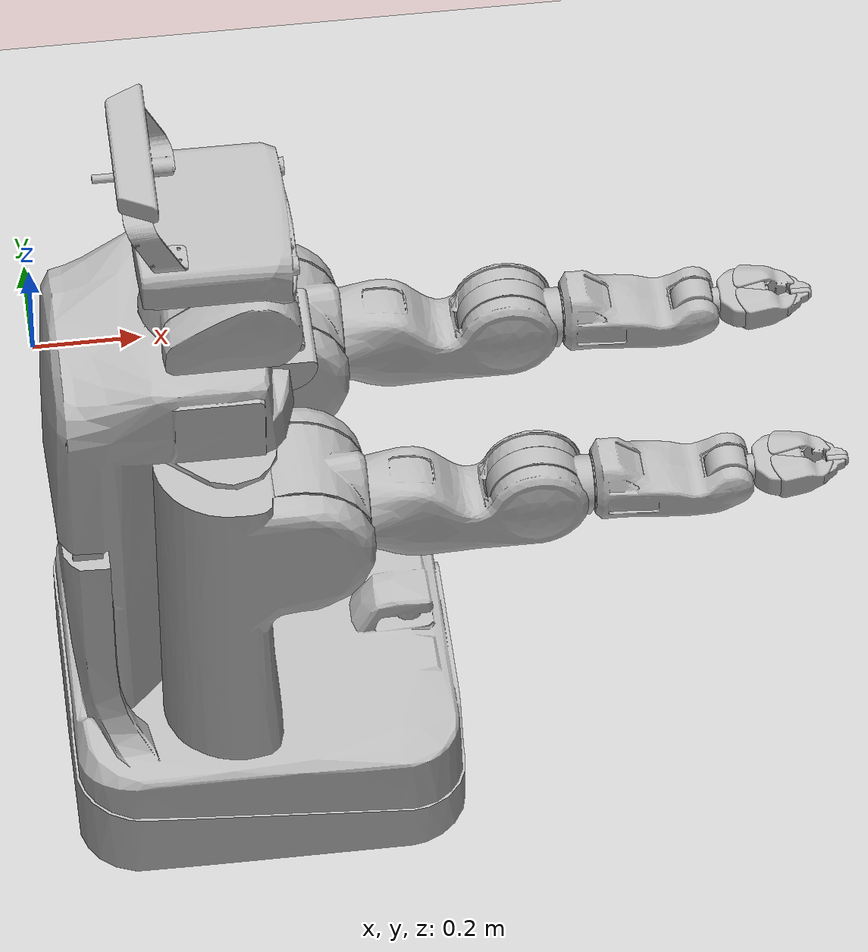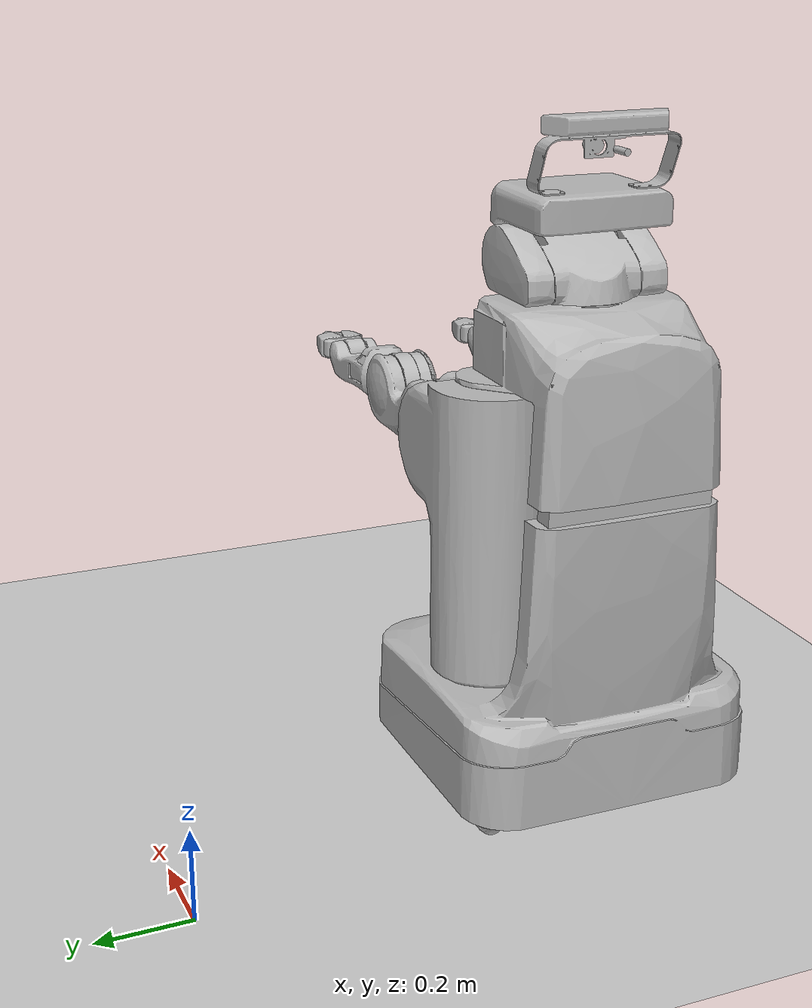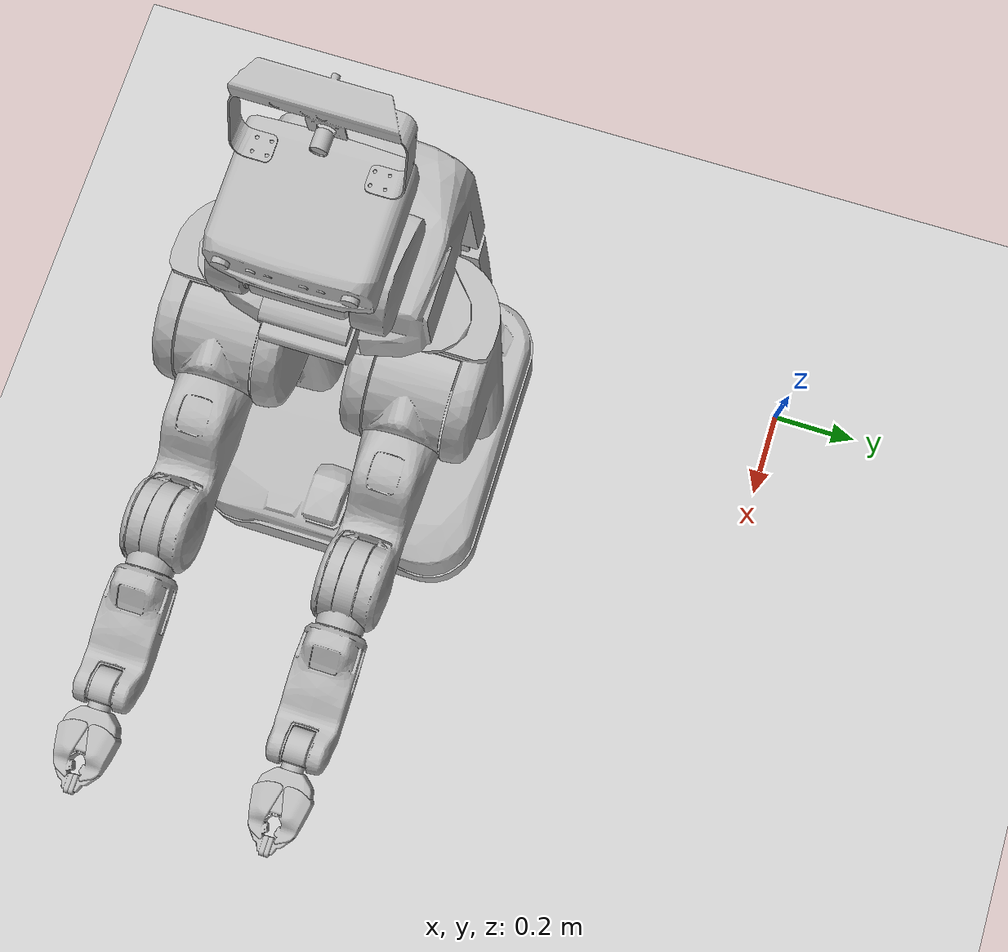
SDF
<sdf version="1.7">
 <world name="default">
  <light name="sun" type="directional">
   <pose>0 0 10 0 -0 0</pose>
   <diffuse>0.8 0.8 0.8 1</diffuse>
   <specular>0.2 0.2 0.2 1</specular>
   <attenuation>
    <range>1000</range>
    <constant>0.9</constant>
    <linear>0.01</linear>
    <quadratic>0.001</quadratic>
   </attenuation>
   <direction>-0.5 0.1 -0.9</direction>
   <spot><inner_angle>0</inner_angle><outer_angle>0</outer_angle><falloff>0</falloff></spot>
  </light>
  <model name="ground_plane">
   <static>1</static>
   <link name="link">
    <collision name="collision">
     <geometry><plane><normal>0 0 1</normal><size>100 100</size></plane></geometry>
     <surface>
      <contact><collide_bitmask>65535</collide_bitmask></contact>
      <friction><ode><mu>100</mu><mu2>50</mu2></ode></friction>
     </surface>
    </collision>
    <visual name="visual">
     <cast_shadows>0</cast_shadows>
     <geometry><plane><normal>0 0 1</normal><size>100 100</size></plane></geometry>
     <material>
      <script><uri>file://media/materials/scripts/gazebo.material</uri><name>Gazebo/Grey</name></script>
     </material>
    </visual>
   </link>
  </model>
  <gravity>0 0 -9.8</gravity>
  <magnetic_field>6e-06 2.3e-05 -4.2e-05</magnetic_field>
  <atmosphere type="adiabatic"/>
  <physics type="ode">
   <max_step_size>0.001</max_step_size>
   <real_time_factor>1</real_time_factor>
   <real_time_update_rate>1000</real_time_update_rate>
  </physics>
  <scene><ambient>0.4 0.4 0.4 1</ambient><background>0.7 0.7 0.7 1</background><shadows>1</shadows></scene>
  <spherical_coordinates>
   <surface_model>EARTH_WGS84</surface_model>
   <latitude_deg>0</latitude_deg>
   <longitude_deg>0</longitude_deg>
   <elevation>0</elevation>
   <heading_deg>0</heading_deg>
  </spherical_coordinates>
  <model name="pr2">
   <static>0</static>
   <link name="base_footprint">
    <inertial>
     <mass>118.001</mass>
     <pose>-0.062421 0 0.201365 0 -0 0</pose>
     <inertia>
      <ixx>8.43173</ixx>
      <ixy>-0.00972</ixy>
      <ixz>1.90157</ixz>
      <iyy>8.53305</iyy>
      <iyz>-0.00738</iyz>
      <izz>3.78747</izz>
     </inertia>
    </inertial>
    <collision name="base_footprint_geom">
     <pose>0 0 0.071 0 -0 0</pose>
     <geometry><box><size>0.001 0.001 0.001</size></box></geometry>
    </collision>
    <visual name="base_footprint_geom_visual"><geometry><box><size>0.01 0.01 0.01</size></box></geometry></visual>
    <collision name="base_footprint_geom_base_bellow_link">
     <pose>-0.29 0 0.851 0 -0 0</pose>
     <geometry><box><size>0.05 0.37 0.3</size></box></geometry>
    </collision>
    <visual name="base_footprint_geom_base_bellow_link_visual">
     <pose>-0.29 0 0.851 0 -0 0</pose>
     <geometry><box><size>0.05 0.37 0.3</size></box></geometry>
    </visual>
    <collision name="base_footprint_geom_base_link">
     <pose>0 0 0.051 0 -0 0</pose>
     <geometry><mesh><uri>model://pr2/meshes/base_v0/base_L.stl</uri></mesh></geometry>
    </collision>
    <visual name="base_footprint_geom_base_link_visual">
     <pose>0 0 0.051 0 -0 0</pose>
     <geometry><mesh><uri>model://pr2/meshes/base_v0/base.dae</uri></mesh></geometry>
    </visual>
    <sensor name="base_contact_sensor" type="contact">
     <update_rate>100</update_rate>
     <contact><collision>base_footprint_geom_base_link</collision><topic>__default_topic__</topic></contact>
     <plugin name="gazebo_contact" filename="libContactPlugin.so"/>
    </sensor>
    <sensor name="base_laser" type="ray">
     <always_on>1</always_on>
     <visualize>1</visualize>
     <update_rate>20</update_rate>
     <pose>0.275 0 0.303 0 -0 0</pose>
     <ray>
      <scan>
       <horizontal>
        <samples>640</samples>
        <resolution>1</resolution>
        <min_angle>-2.2689</min_angle>
        <max_angle>2.2689</max_angle>
       </horizontal>
       <vertical><samples>1</samples><min_angle>0</min_angle><max_angle>0</max_angle></vertical>
      </scan>
      <range><min>0.08</min><max>10</max><resolution>0.01</resolution></range>
     </ray>
     <plugin name="laser" filename="libRayPlugin.so"/>
    </sensor>
   </link>
   <link name="bl_caster_rotation_link">
    <pose>-0.2246 0.2246 0.0792 0 -0 0</pose>
    <inertial>
     <mass>3.47308</mass>
     <pose>0 0 0.07 0 -0 0</pose>
     <inertia>
      <ixx>0.012412</ixx>
      <ixy>-0.000712</ixy>
      <ixz>0.000503</ixz>
      <iyy>0.015218</iyy>
      <iyz>-4e-06</iyz>
      <izz>0.011764</izz>
     </inertia>
    </inertial>
    <collision name="bl_caster_rotation_link_geom">
     <geometry><mesh><uri>model://pr2/meshes/base_v0/caster_L.stl</uri></mesh></geometry>
    </collision>
    <visual name="bl_caster_rotation_link_geom_visual">
     <geometry><mesh><uri>model://pr2/meshes/base_v0/caster.stl</uri></mesh></geometry>
    </visual>
   </link>
   <link name="bl_caster_l_wheel_link">
    <pose>-0.2246 0.2736 0.0792 0 -0 0</pose>
    <inertial>
     <mass>0.44036</mass>
     <inertia>
      <ixx>0.012412</ixx>
      <ixy>-0.000712</ixy>
      <ixz>0.000503</ixz>
      <iyy>0.015218</iyy>
      <iyz>-4e-06</iyz>
      <izz>0.011764</izz>
     </inertia>
    </inertial>
    <collision name="bl_caster_l_wheel_link_geom">
     <pose>0 0 0 1.5708 -0 0</pose>
     <geometry><cylinder><radius>0.074792</radius><length>0.034</length></cylinder></geometry>
    </collision>
    <visual name="bl_caster_l_wheel_link_geom_visual">
     <geometry><mesh><uri>model://pr2/meshes/base_v0/wheel.dae</uri></mesh></geometry>
    </visual>
   </link>
   <link name="bl_caster_r_wheel_link">
    <pose>-0.2246 0.1756 0.0792 0 -0 0</pose>
    <inertial>
     <mass>0.44036</mass>
     <inertia>
      <ixx>0.012412</ixx>
      <ixy>0.000712</ixy>
      <ixz>0.000503</ixz>
      <iyy>0.015218</iyy>
      <iyz>4e-06</iyz>
      <izz>0.011764</izz>
     </inertia>
    </inertial>
    <collision name="bl_caster_r_wheel_link_geom">
     <pose>0 0 0 1.5708 -0 0</pose>
     <geometry><cylinder><radius>0.074792</radius><length>0.034</length></cylinder></geometry>
    </collision>
    <visual name="bl_caster_r_wheel_link_geom_visual">
     <geometry><mesh><uri>model://pr2/meshes/base_v0/wheel.dae</uri></mesh></geometry>
    </visual>
   </link>
   <link name="br_caster_rotation_link">
    <pose>-0.2246 -0.2246 0.0792 0 -0 0</pose>
    <inertial>
     <mass>3.47308</mass>
     <pose>0 0 0.07 0 -0 0</pose>
     <inertia>
      <ixx>0.012412</ixx>
      <ixy>-0.000712</ixy>
      <ixz>0.000503</ixz>
      <iyy>0.015218</iyy>
      <iyz>-4e-06</iyz>
      <izz>0.011764</izz>
     </inertia>
    </inertial>
    <collision name="br_caster_rotation_link_geom">
     <geometry><mesh><uri>model://pr2/meshes/base_v0/caster_L.stl</uri></mesh></geometry>
    </collision>
    <visual name="br_caster_rotation_link_geom_visual">
     <geometry><mesh><uri>model://pr2/meshes/base_v0/caster.stl</uri></mesh></geometry>
    </visual>
   </link>
   <link name="br_caster_l_wheel_link">
    <pose>-0.2246 -0.1756 0.0792 0 -0 0</pose>
    <inertial>
     <mass>0.44036</mass>
     <inertia>
      <ixx>0.012412</ixx>
      <ixy>-0.000712</ixy>
      <ixz>0.000503</ixz>
      <iyy>0.015218</iyy>
      <iyz>-4e-06</iyz>
      <izz>0.011764</izz>
     </inertia>
    </inertial>
    <collision name="br_caster_l_wheel_link_geom">
     <pose>0 0 0 1.5708 -0 0</pose>
     <geometry><cylinder><radius>0.074792</radius><length>0.034</length></cylinder></geometry>
    </collision>
    <visual name="br_caster_l_wheel_link_geom_visual">
     <geometry><mesh><uri>model://pr2/meshes/base_v0/wheel.dae</uri></mesh></geometry>
    </visual>
   </link>
   <link name="br_caster_r_wheel_link">
    <pose>-0.2246 -0.2736 0.0792 0 -0 0</pose>
    <inertial>
     <mass>0.44036</mass>
     <inertia>
      <ixx>0.012412</ixx>
      <ixy>-0.000712</ixy>
      <ixz>0.000503</ixz>
      <iyy>0.015218</iyy>
      <iyz>-4e-06</iyz>
      <izz>0.011764</izz>
     </inertia>
    </inertial>
    <collision name="br_caster_r_wheel_link_geom">
     <pose>0 0 0 1.5708 -0 0</pose>
     <geometry><cylinder><radius>0.074792</radius><length>0.034</length></cylinder></geometry>
    </collision>
    <visual name="br_caster_r_wheel_link_geom_visual">
     <geometry><mesh><uri>model://pr2/meshes/base_v0/wheel.dae</uri></mesh></geometry>
    </visual>
   </link>
   <link name="fl_caster_rotation_link">
    <pose>0.2246 0.2246 0.0792 0 -0 0</pose>
    <inertial>
     <mass>3.47308</mass>
     <pose>0 0 0.07 0 -0 0</pose>
     <inertia>
      <ixx>0.012412</ixx>
      <ixy>-0.000712</ixy>
      <ixz>0.000503</ixz>
      <iyy>0.015218</iyy>
      <iyz>-4e-06</iyz>
      <izz>0.011764</izz>
     </inertia>
    </inertial>
    <collision name="fl_caster_rotation_link_geom">
     <geometry><mesh><uri>model://pr2/meshes/base_v0/caster_L.stl</uri></mesh></geometry>
    </collision>
    <visual name="fl_caster_rotation_link_geom_visual">
     <geometry><mesh><uri>model://pr2/meshes/base_v0/caster.stl</uri></mesh></geometry>
    </visual>
   </link>
   <link name="fl_caster_l_wheel_link">
    <pose>0.2246 0.2736 0.0792 0 -0 0</pose>
    <inertial>
     <mass>0.44036</mass>
     <inertia>
      <ixx>0.012412</ixx>
      <ixy>-0.000712</ixy>
      <ixz>0.000503</ixz>
      <iyy>0.015218</iyy>
      <iyz>-4e-06</iyz>
      <izz>0.011764</izz>
     </inertia>
    </inertial>
    <collision name="fl_caster_l_wheel_link_geom">
     <pose>0 0 0 1.5708 -0 0</pose>
     <geometry><cylinder><radius>0.074792</radius><length>0.034</length></cylinder></geometry>
    </collision>
    <visual name="fl_caster_l_wheel_link_geom_visual">
     <geometry><mesh><uri>model://pr2/meshes/base_v0/wheel.dae</uri></mesh></geometry>
    </visual>
   </link>
   <link name="fl_caster_r_wheel_link">
    <pose>0.2246 0.1756 0.0792 0 -0 0</pose>
    <inertial>
     <mass>0.44036</mass>
     <inertia>
      <ixx>0.012412</ixx>
      <ixy>-0.000712</ixy>
      <ixz>0.000503</ixz>
      <iyy>0.015218</iyy>
      <iyz>-4e-06</iyz>
      <izz>0.011764</izz>
     </inertia>
    </inertial>
    <collision name="fl_caster_r_wheel_link_geom">
     <pose>0 0 0 1.5708 -0 0</pose>
     <geometry><cylinder><radius>0.074792</radius><length>0.034</length></cylinder></geometry>
    </collision>
    <visual name="fl_caster_r_wheel_link_geom_visual">
     <geometry><mesh><uri>model://pr2/meshes/base_v0/wheel.dae</uri></mesh></geometry>
    </visual>
   </link>
   <link name="fr_caster_rotation_link">
    <pose>0.2246 -0.2246 0.0792 0 -0 0</pose>
    <inertial>
     <mass>3.47308</mass>
     <pose>0 0 0.07 0 -0 0</pose>
     <inertia>
      <ixx>0.012412</ixx>
      <ixy>-0.000712</ixy>
      <ixz>0.000503</ixz>
      <iyy>0.015218</iyy>
      <iyz>-4e-06</iyz>
      <izz>0.011764</izz>
     </inertia>
    </inertial>
    <collision name="fr_caster_rotation_link_geom">
     <geometry><mesh><uri>model://pr2/meshes/base_v0/caster_L.stl</uri></mesh></geometry>
    </collision>
    <visual name="fr_caster_rotation_link_geom_visual">
     <geometry><mesh><uri>model://pr2/meshes/base_v0/caster.stl</uri></mesh></geometry>
    </visual>
   </link>
   <link name="fr_caster_l_wheel_link">
    <pose>0.2246 -0.1756 0.0792 0 -0 0</pose>
    <inertial>
     <mass>0.44036</mass>
     <inertia>
      <ixx>0.012412</ixx>
      <ixy>-0.000712</ixy>
      <ixz>0.000503</ixz>
      <iyy>0.015218</iyy>
      <iyz>-4e-06</iyz>
      <izz>0.011764</izz>
     </inertia>
    </inertial>
    <collision name="fr_caster_l_wheel_link_geom">
     <pose>0 0 0 1.5708 -0 0</pose>
     <geometry><cylinder><radius>0.074792</radius><length>0.034</length></cylinder></geometry>
    </collision>
    <visual name="fr_caster_l_wheel_link_geom_visual">
     <geometry><mesh><uri>model://pr2/meshes/base_v0/wheel.dae</uri></mesh></geometry>
    </visual>
   </link>
   <link name="fr_caster_r_wheel_link">
    <pose>0.2246 -0.2736 0.0792 0 -0 0</pose>
    <inertial>
     <mass>0.44036</mass>
     <inertia>
      <ixx>0.012412</ixx>
      <ixy>-0.000712</ixy>
      <ixz>0.000503</ixz>
      <iyy>0.015218</iyy>
      <iyz>-4e-06</iyz>
      <izz>0.011764</izz>
     </inertia>
    </inertial>
    <collision name="fr_caster_r_wheel_link_geom">
     <pose>0 0 0 1.5708 -0 0</pose>
     <geometry><cylinder><radius>0.074792</radius><length>0.034</length></cylinder></geometry>
    </collision>
    <visual name="fr_caster_r_wheel_link_geom_visual">
     <geometry><mesh><uri>model://pr2/meshes/base_v0/wheel.dae</uri></mesh></geometry>
    </visual>
   </link>
   <link name="torso_lift_link">
    <pose>-0.05 0 0.790675 0 -0 0</pose>
    <inertial>
     <mass>36.449</mass>
     <pose>-0.099499 -4e-06 -0.086764 0 -0 0</pose>
     <inertia>
      <ixx>2.79233</ixx>
      <ixy>0.00428</ixy>
      <ixz>-0.160631</ixz>
      <iyy>2.52106</iyy>
      <iyz>0.029689</iyz>
      <izz>0.536551</izz>
     </inertia>
    </inertial>
    <collision name="torso_lift_link_geom">
     <geometry><mesh><uri>model://pr2/meshes/torso_v0/torso_lift_L.stl</uri></mesh></geometry>
    </collision>
    <visual name="torso_lift_link_geom_visual">
     <geometry><mesh><uri>model://pr2/meshes/torso_v0/torso_lift.dae</uri></mesh></geometry>
    </visual>
    <sensor name="torso_lift_contact_sensor" type="contact">
     <update_rate>100</update_rate>
     <contact><collision>torso_lift_link_geom</collision><topic>__default_topic__</topic></contact>
    </sensor>
   </link>
   <link name="head_pan_link">
    <pose>-0.06707 0 1.17213 0 -0 0</pose>
    <inertial>
     <mass>6.339</mass>
     <pose>0.010907 0.031693 0.090507 0 -0 0</pose>
     <inertia>
      <ixx>0.032498</ixx>
      <ixy>0.000636</ixy>
      <ixz>0.002585</ixz>
      <iyy>0.046546</iyy>
      <iyz>-0.002453</iyz>
      <izz>0.057653</izz>
     </inertia>
    </inertial>
    <collision name="head_pan_link_geom">
     <geometry><mesh><uri>model://pr2/meshes/head_v0/head_pan_L.stl</uri></mesh></geometry>
    </collision>
    <visual name="head_pan_link_geom_visual">
     <geometry><mesh><uri>model://pr2/meshes/head_v0/head_pan.dae</uri></mesh></geometry>
    </visual>
   </link>
   <link name="head_tilt_link">
    <projector name="projector_wg6802418_projector_wg6802418">
     <texture>stereo_projection_pattern_high_res_red.png</texture>
     <fov>0.959931</fov>
     <near_clip>0.1</near_clip>
     <far_clip>10</far_clip>
     <pose>0.0232 0.11 0.1191 0 -1.57079 0</pose>
    </projector>
    <pose>0.00093 0 1.17213 0 -0 0</pose>
    <inertial>
     <mass>5.319</mass>
     <pose>-0.005151 -0.014635 0.072819 0 -0 0</pose>
     <inertia>
      <ixx>0.126134</ixx>
      <ixy>0.000237</ixy>
      <ixz>0.011881</ixz>
      <iyy>0.165102</iyy>
      <iyz>0.001606</iyz>
      <izz>0.166947</izz>
     </inertia>
    </inertial>
    <collision name="head_tilt_link_geom">
     <geometry><mesh><uri>model://pr2/meshes/head_v0/head_tilt_L.stl</uri></mesh></geometry>
    </collision>
    <visual name="head_tilt_link_geom_visual">
     <geometry><mesh><uri>model://pr2/meshes/head_v0/head_tilt.dae</uri></mesh></geometry>
    </visual>
    <collision name="head_tilt_link_geom_head_mount_kinect_ir_link">
     <pose>-0.147067 0.0125 0.291953 0 -0 0</pose>
     <geometry><sphere><radius>0.0005</radius></sphere></geometry>
    </collision>
    <visual name="head_tilt_link_geom_head_mount_kinect_ir_link_visual">
     <pose>-0.147067 0.0125 0.291953 0 -0 0</pose>
     <geometry><sphere><radius>0.00025</radius></sphere></geometry>
     <material><script><name>Gazebo/Red</name><uri>__default__</uri></script></material>
    </visual>
    <collision name="head_tilt_link_geom_head_mount_kinect_rgb_link">
     <pose>-0.147067 0.0175 0.291953 0 -0 0</pose>
     <geometry><sphere><radius>0.0005</radius></sphere></geometry>
    </collision>
    <visual name="head_tilt_link_geom_head_mount_kinect_rgb_link_visual">
     <pose>-0.147067 0.0175 0.291953 0 -0 0</pose>
     <geometry><sphere><radius>0.00025</radius></sphere></geometry>
     <material><script><name>Gazebo/Red</name><uri>__default__</uri></script></material>
    </visual>
    <collision name="head_tilt_link_geom_head_mount_link">
     <pose>-0.1148 0 0.1555 0 -0 0</pose>
     <geometry><sphere><radius>0.0005</radius></sphere></geometry>
    </collision>
    <visual name="head_tilt_link_geom_head_mount_link_visual">
     <pose>-0.1148 0 0.1555 0 -0 0</pose>
     <geometry>
      <mesh>
       <uri>model://pr2/meshes/sensors/kinect_prosilica_v0/115x100_swept_back--coarse.STL</uri>
       <scale>0.001 0.001 0.001</scale>
      </mesh>
     </geometry>
    </visual>
    <collision name="head_tilt_link_geom_head_mount_prosilica_link">
     <pose>-0.161257 0.0125 0.244421 0 -0 0</pose>
     <geometry><sphere><radius>0.0005</radius></sphere></geometry>
    </collision>
    <visual name="head_tilt_link_geom_head_mount_prosilica_link_visual">
     <pose>-0.161257 0.0125 0.244421 0 -0 0</pose>
     <geometry><sphere><radius>0.00025</radius></sphere></geometry>
     <material><script><name>Gazebo/Red</name><uri>__default__</uri></script></material>
    </visual>
    <collision name="head_tilt_link_geom_head_plate_frame">
     <pose>0.0232 0 0.0645 0 -0 0</pose>
     <geometry><box><size>0.01 0.01 0.01</size></box></geometry>
    </collision>
    <visual name="head_tilt_link_geom_head_plate_frame_visual">
     <pose>0.0232 0 0.0645 0 -0 0</pose>
     <geometry><box><size>0.01 0.01 0.01</size></box></geometry>
     <material><script><name>Gazebo/Grey</name><uri>__default__</uri></script></material>
    </visual>
    <sensor name="head_mount_sensor" type="camera">
     <always_on>0</always_on>
     <visualize>0</visualize>
     <update_rate>1</update_rate>
     <pose>-0.147067 0.0125 0.291953 0 -0 0</pose>
     <camera>
      <horizontal_fov>0.994838</horizontal_fov>
      <image><width>640</width><height>480</height><format>L8</format></image>
      <clip><near>0.01</near><far>5</far></clip>
     </camera>
    </sensor>
    <sensor name="head_mount_prosilica_link_sensor" type="camera">
     <update_rate>1</update_rate>
     <pose>-0.161257 0.0125 0.244421 0 -0 0</pose>
     <camera>
      <horizontal_fov>1.1205</horizontal_fov>
      <image><width>320</width><height>240</height><format>R8G8B8</format></image>
      <clip><near>0.1</near><far>100</far></clip>
     </camera>
    </sensor>
    <sensor name="head_mount_prosilica_link_sim_pcd_sensor" type="camera">
     <update_rate>1</update_rate>
     <pose>-0.161257 0.0125 0.244421 0 -0 0</pose>
     <camera>
      <horizontal_fov>1.1205</horizontal_fov>
      <image><width>320</width><height>240</height><format>R8G8B8</format></image>
      <clip><near>0.1</near><far>100</far></clip>
     </camera>
    </sensor>
    <sensor name="narrow_stereo_gazebo_l_stereo_camera_sensor" type="camera">
     <always_on>1</always_on>
     <visualize>1</visualize>
     <update_rate>25</update_rate>
     <pose>0.0682 0.06 0.1146 0 -0 0</pose>
     <camera>
      <horizontal_fov>0.785398</horizontal_fov>
      <image><width>640</width><height>480</height><format>L8</format></image>
      <clip><near>0.1</near><far>100</far></clip>
     </camera>
    </sensor>
    <sensor name="narrow_stereo_gazebo_r_stereo_camera_sensor" type="camera">
     <always_on>1</always_on>
     <update_rate>25</update_rate>
     <pose>0.0682 -0.03 0.1146 0 -0 0</pose>
     <camera>
      <horizontal_fov>0.785398</horizontal_fov>
      <image><width>640</width><height>480</height><format>L8</format></image>
      <clip><near>0.1</near><far>100</far></clip>
     </camera>
    </sensor>
    <sensor name="wide_stereo_gazebo_l_stereo_camera_sensor" type="camera">
     <update_rate>25</update_rate>
     <pose>0.0682 0.03 0.1146 0 -0 0</pose>
     <camera>
      <horizontal_fov>1.5708</horizontal_fov>
      <image><width>640</width><height>480</height><format>BAYER_BGGR8</format></image>
      <clip><near>0.1</near><far>100</far></clip>
     </camera>
    </sensor>
    <sensor name="wide_stereo_gazebo_r_stereo_camera_sensor" type="camera">
     <update_rate>25</update_rate>
     <pose>0.0682 -0.06 0.1146 0 -0 0</pose>
     <camera>
      <horizontal_fov>1.5708</horizontal_fov>
      <image><width>640</width><height>480</height><format>BAYER_BGGR8</format></image>
      <clip><near>0.1</near><far>100</far></clip>
     </camera>
    </sensor>
    <sensor name="high_def_sensor" type="camera">
     <update_rate>20</update_rate>
     <pose>0.069657 -0.11 0.1191 0 -0 0</pose>
     <camera>
      <horizontal_fov>0.785398</horizontal_fov>
      <image><width>2448</width><height>2050</height><format>R8G8B8</format></image>
      <clip><near>0.1</near><far>100</far></clip>
     </camera>
    </sensor>
   </link>
   <link name="l_shoulder_pan_link">
    <gravity>0</gravity>
    <pose>-0.05 0.188 0.790675 0 -0 0</pose>
    <inertial>
     <mass>25.7993</mass>
     <pose>-0.001201 0.024513 -0.098231 0 -0 0</pose>
     <inertia>
      <ixx>0.866179</ixx>
      <ixy>-0.060865</ixy>
      <ixz>-0.121181</ixz>
      <iyy>0.874217</iyy>
      <iyz>-0.058866</iyz>
      <izz>0.273538</izz>
     </inertia>
    </inertial>
    <collision name="l_shoulder_pan_link_geom">
     <geometry><mesh><uri>model://pr2/meshes/shoulder_v0/shoulder_pan.stl</uri></mesh></geometry>
    </collision>
    <visual name="l_shoulder_pan_link_geom_visual">
     <geometry><mesh><uri>model://pr2/meshes/shoulder_v0/shoulder_pan.dae</uri></mesh></geometry>
    </visual>
   </link>
   <link name="l_shoulder_lift_link">
    <gravity>0</gravity>
    <pose>0.05 0.188 0.790675 0 -0 0</pose>
    <inertial>
     <mass>2.74988</mass>
     <pose>0.02195 -0.02664 -0.03127 0 -0 0</pose>
     <inertia>
      <ixx>0.021056</ixx>
      <ixy>0.004967</ixy>
      <ixz>-0.001948</ixz>
      <iyy>0.021272</iyy>
      <iyz>0.001104</iyz>
      <izz>0.019758</izz>
     </inertia>
    </inertial>
    <collision name="l_shoulder_lift_link_geom">
     <geometry><mesh><uri>model://pr2/meshes/shoulder_v0/shoulder_lift.stl</uri></mesh></geometry>
    </collision>
    <visual name="l_shoulder_lift_link_geom_visual">
     <geometry><mesh><uri>model://pr2/meshes/shoulder_v0/shoulder_lift.dae</uri></mesh></geometry>
    </visual>
   </link>
   <link name="l_upper_arm_roll_link">
    <gravity>0</gravity>
    <pose>0.05 0.188 0.790675 0 -0 0</pose>
    <inertial>
     <mass>6.11769</mass>
     <pose>0.210551 0.016309 -0.000561 0 -0 0</pose>
     <inertia>
      <ixx>0.025306</ixx>
      <ixy>-0.003393</ixy>
      <ixz>0.000608</ixz>
      <iyy>0.084737</iyy>
      <iyz>-0.0002</iyz>
      <izz>0.086016</izz>
     </inertia>
    </inertial>
    <collision name="l_upper_arm_roll_link_geom">
     <geometry><mesh><uri>model://pr2/meshes/shoulder_v0/upper_arm_roll_L.stl</uri></mesh></geometry>
    </collision>
    <visual name="l_upper_arm_roll_link_geom_visual">
     <geometry><mesh><uri>model://pr2/meshes/shoulder_v0/upper_arm_roll.stl</uri></mesh></geometry>
    </visual>
    <collision name="l_upper_arm_roll_link_geom_l_upper_arm_link">
     <geometry><mesh><uri>model://pr2/meshes/upper_arm_v0/upper_arm.stl</uri></mesh></geometry>
    </collision>
    <visual name="l_upper_arm_roll_link_geom_l_upper_arm_link_visual">
     <geometry><mesh><uri>model://pr2/meshes/upper_arm_v0/upper_arm.dae</uri></mesh></geometry>
    </visual>
   </link>
   <link name="l_elbow_flex_link">
    <gravity>0</gravity>
    <pose>0.45 0.188 0.790675 0 -0 0</pose>
    <inertial>
     <mass>1.90327</mass>
     <pose>0.01014 0.00032 -0.01211 0 -0 0</pose>
     <inertia>
      <ixx>0.003465</ixx>
      <ixy>4.1e-05</ixy>
      <ixz>0.000432</ixz>
      <iyy>0.004416</iyy>
      <iyz>-4e-05</iyz>
      <izz>0.003592</izz>
     </inertia>
    </inertial>
    <collision name="l_elbow_flex_link_geom">
     <geometry><mesh><uri>model://pr2/meshes/upper_arm_v0/elbow_flex.stl</uri></mesh></geometry>
    </collision>
    <visual name="l_elbow_flex_link_geom_visual">
     <geometry><mesh><uri>model://pr2/meshes/upper_arm_v0/elbow_flex.dae</uri></mesh></geometry>
    </visual>
   </link>
   <link name="l_forearm_roll_link">
    <gravity>0</gravity>
    <pose>0.45 0.188 0.790675 0 -0 0</pose>
    <inertial>
     <mass>2.68968</mass>
     <pose>0.180727 -0.000163 -0.008583 0 -0 0</pose>
     <inertia>
      <ixx>0.014668</ixx>
      <ixy>5.2e-05</ixy>
      <ixz>0.000656</ixz>
      <iyy>0.026279</iyy>
      <iyz>-1.3e-05</iyz>
      <izz>0.027775</izz>
     </inertia>
    </inertial>
    <collision name="l_forearm_roll_link_geom">
     <geometry><mesh><uri>model://pr2/meshes/upper_arm_v0/forearm_roll_L.stl</uri></mesh></geometry>
    </collision>
    <visual name="l_forearm_roll_link_geom_visual">
     <geometry><mesh><uri>model://pr2/meshes/upper_arm_v0/forearm_roll.stl</uri></mesh></geometry>
    </visual>
    <collision name="l_forearm_roll_link_geom_l_forearm_link">
     <geometry><mesh><uri>model://pr2/meshes/forearm_v0/forearm.stl</uri></mesh></geometry>
    </collision>
    <visual name="l_forearm_roll_link_geom_l_forearm_link_visual">
     <geometry><mesh><uri>model://pr2/meshes/forearm_v0/forearm.dae</uri></mesh></geometry>
    </visual>
    <sensor name="l_forearm_cam_sensor" type="camera">
     <update_rate>25</update_rate>
     <pose>0.135 0 0.044 -1.5708 -0.562869 0</pose>
     <camera>
      <horizontal_fov>1.5708</horizontal_fov>
      <image><width>640</width><height>480</height><format>R8G8B8</format></image>
      <clip><near>0.1</near><far>100</far></clip>
     </camera>
    </sensor>
   </link>
   <link name="l_wrist_flex_link">
    <gravity>0</gravity>
    <pose>0.771 0.188 0.790675 0 -0 0</pose>
    <inertial>
     <mass>0.61402</mass>
     <pose>-0.00157 0 -0.00075 0 -0 0</pose>
     <inertia>
      <ixx>0.000652</ixx>
      <ixy>0</ixy>
      <ixz>3e-06</ixz>
      <iyy>0.000198</iyy>
      <iyz>0</iyz>
      <izz>0.000645</izz>
     </inertia>
    </inertial>
    <collision name="l_wrist_flex_link_geom">
     <geometry><mesh><uri>model://pr2/meshes/forearm_v0/wrist_flex.stl</uri></mesh></geometry>
    </collision>
    <visual name="l_wrist_flex_link_geom_visual">
     <geometry><mesh><uri>model://pr2/meshes/forearm_v0/wrist_flex.dae</uri></mesh></geometry>
    </visual>
   </link>
   <link name="l_wrist_roll_link">
    <gravity>0</gravity>
    <pose>0.771 0.188 0.790675 0 -0 0</pose>
    <inertial>
     <mass>0.68107</mass>
     <pose>0.056408 0.000451 -0.001014 0 -0 0</pose>
     <inertia>
      <ixx>0.011352</ixx>
      <ixy>-1.6e-05</ixy>
      <ixz>-1e-06</ixz>
      <iyy>0.011677</iyy>
      <iyz>-1e-06</iyz>
      <izz>0.011866</izz>
     </inertia>
    </inertial>
    <collision name="l_wrist_roll_link_geom">
     <geometry><mesh><uri>model://pr2/meshes/forearm_v0/wrist_roll_L.stl</uri></mesh></geometry>
    </collision>
    <visual name="l_wrist_roll_link_geom_visual">
     <geometry><mesh><uri>model://pr2/meshes/forearm_v0/wrist_roll.stl</uri></mesh></geometry>
    </visual>
    <collision name="l_wrist_roll_link_geom_l_gripper_motor_accelerometer_link">
     <geometry><box><size>0.001 0.001 0.001</size></box></geometry>
    </collision>
    <visual name="l_wrist_roll_link_geom_l_gripper_motor_accelerometer_link_visual">
     <geometry><box><size>0.001 0.001 0.001</size></box></geometry>
    </visual>
    <collision name="l_wrist_roll_link_geom_l_gripper_palm_link">
     <geometry><mesh><uri>model://pr2/meshes/gripper_v0/gripper_palm.stl</uri></mesh></geometry>
    </collision>
    <visual name="l_wrist_roll_link_geom_l_gripper_palm_link_visual">
     <geometry><mesh><uri>model://pr2/meshes/gripper_v0/gripper_palm.dae</uri></mesh></geometry>
    </visual>
   </link>
   <link name="l_gripper_l_finger_link">
    <gravity>0</gravity>
    <pose>0.84791 0.198 0.790675 0 -0 0</pose>
    <inertial>
     <mass>0.17126</mass>
     <pose>0.03598 0.0173 -0.00164 0 -0 0</pose>
     <inertia>
      <ixx>7.8e-05</ixx>
      <ixy>1e-06</ixy>
      <ixz>-1e-05</ixz>
      <iyy>0.000197</iyy>
      <iyz>-3e-06</iyz>
      <izz>0.000181</izz>
     </inertia>
    </inertial>
    <collision name="l_gripper_l_finger_link_geom">
     <geometry><mesh><uri>model://pr2/meshes/gripper_v0/l_finger.stl</uri></mesh></geometry>
     <surface>
      <friction><ode><mu>500</mu><mu2>500</mu2><slip1>0</slip1><slip2>0</slip2></ode></friction>
      <contact><ode><kp>1e+06</kp><kd>1</kd><max_vel>100</max_vel><min_depth>0</min_depth></ode></contact>
     </surface>
    </collision>
    <visual name="l_gripper_l_finger_link_geom_visual">
     <geometry><mesh><uri>model://pr2/meshes/gripper_v0/l_finger.dae</uri></mesh></geometry>
    </visual>
   </link>
   <link name="l_gripper_l_finger_tip_link">
    <gravity>0</gravity>
    <pose>0.93928 0.20295 0.790675 0 -0 0</pose>
    <inertial>
     <mass>0.04419</mass>
     <pose>0.00423 0.00284 0 0 -0 0</pose>
     <inertia><ixx>8e-06</ixx><ixy>6e-06</ixy><ixz>0</ixz><iyy>1e-05</iyy><iyz>0</iyz><izz>1.5e-05</izz></inertia>
    </inertial>
    <collision name="l_gripper_l_finger_tip_link_geom">
     <geometry><mesh><uri>model://pr2/meshes/gripper_v0/l_finger_tip.stl</uri></mesh></geometry>
     <surface>
      <friction><ode><mu>500</mu><mu2>500</mu2><slip1>0</slip1><slip2>0</slip2></ode></friction>
      <contact><ode><kp>1e+07</kp><kd>1</kd><max_vel>100</max_vel><min_depth>0</min_depth></ode></contact>
     </surface>
    </collision>
    <visual name="l_gripper_l_finger_tip_link_geom_visual">
     <geometry><mesh><uri>model://pr2/meshes/gripper_v0/l_finger_tip.dae</uri></mesh></geometry>
    </visual>
    <sensor name="l_gripper_l_finger_tip_contact_sensor" type="contact">
     <update_rate>100</update_rate>
     <contact><collision>l_gripper_l_finger_tip_link_geom</collision><topic>__default_topic__</topic></contact>
    </sensor>
   </link>
   <link name="l_gripper_motor_slider_link">
    <gravity>0</gravity>
    <pose>0.93928 0.188 0.790675 0 -0 0</pose>
    <inertial>
     <mass>0.01</mass>
     <inertia><ixx>0.001</ixx><ixy>0</ixy><ixz>0</ixz><iyy>0.001</iyy><iyz>0</iyz><izz>0.001</izz></inertia>
    </inertial>
   </link>
   <link name="l_gripper_motor_screw_link">
    <gravity>0</gravity>
    <pose>0.93928 0.188 0.790675 0 -0 0</pose>
    <inertial>
     <mass>0.01</mass>
     <inertia><ixx>0.0001</ixx><ixy>0</ixy><ixz>0</ixz><iyy>0.0001</iyy><iyz>0</iyz><izz>0.0001</izz></inertia>
    </inertial>
   </link>
   <link name="l_gripper_r_finger_link">
    <gravity>0</gravity>
    <pose>0.84791 0.178 0.790675 0 -0 0</pose>
    <inertial>
     <mass>0.17389</mass>
     <pose>0.03576 -0.01736 -0.00095 0 -0 0</pose>
     <inertia>
      <ixx>7.7e-05</ixx>
      <ixy>-2e-06</ixy>
      <ixz>-8e-06</ixz>
      <iyy>0.000198</iyy>
      <iyz>2e-06</iyz>
      <izz>0.000181</izz>
     </inertia>
    </inertial>
    <collision name="l_gripper_r_finger_link_geom">
     <pose>0 0 0 -3.14159 0 0</pose>
     <geometry><mesh><uri>model://pr2/meshes/gripper_v0/l_finger.stl</uri></mesh></geometry>
     <surface>
      <friction><ode><mu>500</mu><mu2>500</mu2><slip1>0</slip1><slip2>0</slip2></ode></friction>
      <contact><ode><kp>1e+06</kp><kd>1</kd><max_vel>100</max_vel><min_depth>0</min_depth></ode></contact>
     </surface>
    </collision>
    <visual name="l_gripper_r_finger_link_geom_visual">
     <pose>0 0 0 -3.14159 0 0</pose>
     <geometry><mesh><uri>model://pr2/meshes/gripper_v0/l_finger.dae</uri></mesh></geometry>
    </visual>
   </link>
   <link name="l_gripper_r_finger_tip_link">
    <gravity>0</gravity>
    <pose>0.93928 0.17305 0.790675 0 -0 0</pose>
    <inertial>
     <mass>0.04419</mass>
     <pose>0.00423 -0.00284 0 0 -0 0</pose>
     <inertia><ixx>8e-06</ixx><ixy>-6e-06</ixy><ixz>0</ixz><iyy>1e-05</iyy><iyz>0</iyz><izz>1.5e-05</izz></inertia>
    </inertial>
    <collision name="l_gripper_r_finger_tip_link_geom">
     <pose>0 0 0 -3.14159 0 0</pose>
     <geometry><mesh><uri>model://pr2/meshes/gripper_v0/l_finger_tip.stl</uri></mesh></geometry>
     <surface>
      <friction><ode><mu>500</mu><mu2>500</mu2><slip1>0</slip1><slip2>0</slip2></ode></friction>
      <contact><ode><kp>1e+07</kp><kd>1</kd><max_vel>100</max_vel><min_depth>0</min_depth></ode></contact>
     </surface>
    </collision>
    <visual name="l_gripper_r_finger_tip_link_geom_visual">
     <pose>0 0 0 -3.14159 0 0</pose>
     <geometry><mesh><uri>model://pr2/meshes/gripper_v0/l_finger_tip.dae</uri></mesh></geometry>
    </visual>
    <sensor name="l_gripper_r_finger_tip_contact_sensor" type="contact">
     <update_rate>100</update_rate>
     <contact><collision>l_gripper_r_finger_tip_link_geom</collision><topic>__default_topic__</topic></contact>
    </sensor>
   </link>
   <link name="laser_tilt_mount_link">
    <pose>0.04893 0 1.01768 0 -0 0</pose>
    <inertial>
     <mass>0.592</mass>
     <pose>-0.001134 0.001667 -0.007067 0 -0 0</pose>
     <inertia>
      <ixx>0.001296</ixx>
      <ixy>2.3e-05</ixy>
      <ixz>3.7e-05</ixz>
      <iyy>0.001086</iyy>
      <iyz>3.5e-05</iyz>
      <izz>0.000895</izz>
     </inertia>
    </inertial>
    <collision name="laser_tilt_mount_link_geom">
     <geometry><mesh><uri>model://pr2/meshes/tilting_laser_v0/tilting_hokuyo_L.stl</uri></mesh></geometry>
     <surface>
      <friction><ode><mu>0</mu><mu2>0</mu2><slip1>0</slip1><slip2>0</slip2></ode></friction>
      <contact><ode><kp>1e+12</kp><kd>10000</kd><max_vel>100</max_vel><min_depth>0</min_depth></ode></contact>
     </surface>
    </collision>
    <visual name="laser_tilt_mount_link_geom_visual">
     <geometry><mesh><uri>model://pr2/meshes/tilting_laser_v0/tilting_hokuyo.dae</uri></mesh></geometry>
    </visual>
    <sensor name="laser_tilt" type="ray">
     <update_rate>40</update_rate>
     <pose>0 0 0.03 0 -0 0</pose>
     <ray>
      <scan>
       <horizontal>
        <samples>640</samples>
        <resolution>1</resolution>
        <min_angle>-1.39626</min_angle>
        <max_angle>1.39626</max_angle>
       </horizontal>
       <vertical><samples>1</samples><min_angle>0</min_angle><max_angle>0</max_angle></vertical>
      </scan>
      <range><min>0.08</min><max>10</max><resolution>0.01</resolution></range>
     </ray>
    </sensor>
   </link>
   <link name="r_shoulder_pan_link">
    <gravity>0</gravity>
    <pose>-0.05 -0.188 0.790675 0 -0 0</pose>
    <inertial>
     <mass>25.7993</mass>
     <pose>-0.001201 0.024513 -0.098231 0 -0 0</pose>
     <inertia>
      <ixx>0.866179</ixx>
      <ixy>-0.060865</ixy>
      <ixz>-0.121181</ixz>
      <iyy>0.874217</iyy>
      <iyz>-0.058866</iyz>
      <izz>0.273538</izz>
     </inertia>
    </inertial>
    <collision name="r_shoulder_pan_link_geom">
     <geometry><mesh><uri>model://pr2/meshes/shoulder_v0/shoulder_pan.stl</uri></mesh></geometry>
     <surface>
      <friction><ode><mu>0</mu><mu2>0</mu2><slip1>0</slip1><slip2>0</slip2></ode></friction>
      <contact><ode><kp>1e+12</kp><kd>10000</kd><max_vel>100</max_vel><min_depth>0</min_depth></ode></contact>
     </surface>
    </collision>
    <visual name="r_shoulder_pan_link_geom_visual">
     <geometry><mesh><uri>model://pr2/meshes/shoulder_v0/shoulder_pan.dae</uri></mesh></geometry>
    </visual>
   </link>
   <link name="r_shoulder_lift_link">
    <gravity>0</gravity>
    <pose>0.05 -0.188 0.790675 0 -0 0</pose>
    <inertial>
     <mass>2.74988</mass>
     <pose>0.02195 -0.02664 -0.03127 0 -0 0</pose>
     <inertia>
      <ixx>0.021056</ixx>
      <ixy>0.004967</ixy>
      <ixz>-0.001948</ixz>
      <iyy>0.021272</iyy>
      <iyz>0.001104</iyz>
      <izz>0.019758</izz>
     </inertia>
    </inertial>
    <collision name="r_shoulder_lift_link_geom">
     <geometry><mesh><uri>model://pr2/meshes/shoulder_v0/shoulder_lift.stl</uri></mesh></geometry>
     <surface>
      <friction><ode><mu>0</mu><mu2>0</mu2><slip1>0</slip1><slip2>0</slip2></ode></friction>
      <contact><ode><kp>1e+12</kp><kd>10000</kd><max_vel>100</max_vel><min_depth>0</min_depth></ode></contact>
     </surface>
    </collision>
    <visual name="r_shoulder_lift_link_geom_visual">
     <geometry><mesh><uri>model://pr2/meshes/shoulder_v0/shoulder_lift.dae</uri></mesh></geometry>
    </visual>
   </link>
   <link name="r_upper_arm_roll_link">
    <gravity>0</gravity>
    <pose>0.05 -0.188 0.790675 0 -0 0</pose>
    <inertial>
     <mass>6.11769</mass>
     <pose>0.210482 -0.015945 -0.000197 0 -0 0</pose>
     <inertia>
      <ixx>0.025378</ixx>
      <ixy>0.003757</ixy>
      <ixz>-0.000709</ixz>
      <iyy>0.084737</iyy>
      <iyz>-0.000179</iyz>
      <izz>0.086088</izz>
     </inertia>
    </inertial>
    <collision name="r_upper_arm_roll_link_geom">
     <geometry><mesh><uri>model://pr2/meshes/shoulder_v0/upper_arm_roll_L.stl</uri></mesh></geometry>
    </collision>
    <visual name="r_upper_arm_roll_link_geom_visual">
     <geometry><mesh><uri>model://pr2/meshes/shoulder_v0/upper_arm_roll.stl</uri></mesh></geometry>
    </visual>
    <collision name="r_upper_arm_roll_link_geom_r_upper_arm_link">
     <geometry><mesh><uri>model://pr2/meshes/upper_arm_v0/upper_arm.stl</uri></mesh></geometry>
    </collision>
    <visual name="r_upper_arm_roll_link_geom_r_upper_arm_link_visual">
     <geometry><mesh><uri>model://pr2/meshes/upper_arm_v0/upper_arm.dae</uri></mesh></geometry>
    </visual>
   </link>
   <link name="r_elbow_flex_link">
    <gravity>0</gravity>
    <pose>0.45 -0.188 0.790675 0 -0 0</pose>
    <inertial>
     <mass>1.90327</mass>
     <pose>0.01014 0.00032 -0.01211 0 -0 0</pose>
     <inertia>
      <ixx>0.003465</ixx>
      <ixy>4.1e-05</ixy>
      <ixz>0.000432</ixz>
      <iyy>0.004416</iyy>
      <iyz>-4e-05</iyz>
      <izz>0.003592</izz>
     </inertia>
    </inertial>
    <collision name="r_elbow_flex_link_geom">
     <geometry><mesh><uri>model://pr2/meshes/upper_arm_v0/elbow_flex.stl</uri></mesh></geometry>
    </collision>
    <visual name="r_elbow_flex_link_geom_visual">
     <geometry><mesh><uri>model://pr2/meshes/upper_arm_v0/elbow_flex.dae</uri></mesh></geometry>
    </visual>
   </link>
   <link name="r_forearm_roll_link">
    <gravity>0</gravity>
    <pose>0.45 -0.188 0.790675 0 -0 0</pose>
    <inertial>
     <mass>2.68968</mass>
     <pose>0.180727 -0.000163 -0.008583 0 -0 0</pose>
     <inertia>
      <ixx>0.014668</ixx>
      <ixy>5.2e-05</ixy>
      <ixz>0.000656</ixz>
      <iyy>0.026279</iyy>
      <iyz>-1.3e-05</iyz>
      <izz>0.027775</izz>
     </inertia>
    </inertial>
    <collision name="r_forearm_roll_link_geom">
     <geometry><mesh><uri>model://pr2/meshes/upper_arm_v0/forearm_roll_L.stl</uri></mesh></geometry>
    </collision>
    <visual name="r_forearm_roll_link_geom_visual">
     <geometry><mesh><uri>model://pr2/meshes/upper_arm_v0/forearm_roll.stl</uri></mesh></geometry>
    </visual>
    <collision name="r_forearm_roll_link_geom_r_forearm_link">
     <geometry><mesh><uri>model://pr2/meshes/forearm_v0/forearm.stl</uri></mesh></geometry>
    </collision>
    <visual name="r_forearm_roll_link_geom_r_forearm_link_visual">
     <geometry><mesh><uri>model://pr2/meshes/forearm_v0/forearm.dae</uri></mesh></geometry>
    </visual>
    <sensor name="r_forearm_cam_sensor" type="camera">
     <update_rate>25</update_rate>
     <pose>0.135 0 0.044 1.5708 -0.562869 -0</pose>
     <camera>
      <horizontal_fov>1.5708</horizontal_fov>
      <image><width>640</width><height>480</height><format>R8G8B8</format></image>
      <clip><near>0.1</near><far>100</far></clip>
     </camera>
    </sensor>
   </link>
   <link name="r_wrist_flex_link">
    <gravity>0</gravity>
    <pose>0.771 -0.188 0.790675 0 -0 0</pose>
    <inertial>
     <mass>0.61402</mass>
     <pose>-0.00157 0 -0.00075 0 -0 0</pose>
     <inertia>
      <ixx>0.000652</ixx>
      <ixy>0</ixy>
      <ixz>3e-06</ixz>
      <iyy>0.000198</iyy>
      <iyz>0</iyz>
      <izz>0.000645</izz>
     </inertia>
    </inertial>
    <collision name="r_wrist_flex_link_geom">
     <geometry><mesh><uri>model://pr2/meshes/forearm_v0/wrist_flex.stl</uri></mesh></geometry>
    </collision>
    <visual name="r_wrist_flex_link_geom_visual">
     <geometry><mesh><uri>model://pr2/meshes/forearm_v0/wrist_flex.dae</uri></mesh></geometry>
    </visual>
   </link>
   <link name="r_wrist_roll_link">
    <gravity>0</gravity>
    <pose>0.771 -0.188 0.790675 0 -0 0</pose>
    <inertial>
     <mass>0.68107</mass>
     <pose>0.056408 0.000451 -0.001014 0 -0 0</pose>
     <inertia>
      <ixx>0.011352</ixx>
      <ixy>-1.6e-05</ixy>
      <ixz>-1e-06</ixz>
      <iyy>0.011677</iyy>
      <iyz>-1e-06</iyz>
      <izz>0.011866</izz>
     </inertia>
    </inertial>
    <collision name="r_wrist_roll_link_geom">
     <geometry><mesh><uri>model://pr2/meshes/forearm_v0/wrist_roll_L.stl</uri></mesh></geometry>
    </collision>
    <visual name="r_wrist_roll_link_geom_visual">
     <geometry><mesh><uri>model://pr2/meshes/forearm_v0/wrist_roll.stl</uri></mesh></geometry>
    </visual>
    <collision name="r_wrist_roll_link_geom_r_gripper_motor_accelerometer_link">
     <geometry><box><size>0.001 0.001 0.001</size></box></geometry>
    </collision>
    <visual name="r_wrist_roll_link_geom_r_gripper_motor_accelerometer_link_visual">
     <geometry><box><size>0.001 0.001 0.001</size></box></geometry>
    </visual>
    <collision name="r_wrist_roll_link_geom_r_gripper_palm_link">
     <geometry><mesh><uri>model://pr2/meshes/gripper_v0/gripper_palm.stl</uri></mesh></geometry>
    </collision>
    <visual name="r_wrist_roll_link_geom_r_gripper_palm_link_visual">
     <geometry><mesh><uri>model://pr2/meshes/gripper_v0/gripper_palm.dae</uri></mesh></geometry>
    </visual>
   </link>
   <link name="r_gripper_l_finger_link">
    <gravity>0</gravity>
    <pose>0.84791 -0.178 0.790675 0 -0 0</pose>
    <inertial>
     <mass>0.17126</mass>
     <pose>0.03598 0.0173 -0.00164 0 -0 0</pose>
     <inertia>
      <ixx>7.8e-05</ixx>
      <ixy>1e-06</ixy>
      <ixz>1e-05</ixz>
      <iyy>0.000197</iyy>
      <iyz>-3e-06</iyz>
      <izz>0.000181</izz>
     </inertia>
    </inertial>
    <collision name="r_gripper_l_finger_link_geom">
     <geometry><mesh><uri>model://pr2/meshes/gripper_v0/l_finger.stl</uri></mesh></geometry>
     <surface>
      <friction><ode><mu>500</mu><mu2>500</mu2><slip1>0</slip1><slip2>0</slip2></ode></friction>
      <contact><ode><kp>1e+06</kp><kd>1</kd><max_vel>100</max_vel><min_depth>0</min_depth></ode></contact>
     </surface>
    </collision>
    <visual name="r_gripper_l_finger_link_geom_visual">
     <geometry><mesh><uri>model://pr2/meshes/gripper_v0/l_finger.dae</uri></mesh></geometry>
    </visual>
   </link>
   <link name="r_gripper_l_finger_tip_link">
    <gravity>0</gravity>
    <pose>0.93928 -0.17305 0.790675 0 -0 0</pose>
    <inertial>
     <mass>0.04419</mass>
     <pose>0.00423 0.00284 0 0 -0 0</pose>
     <inertia><ixx>8e-06</ixx><ixy>6e-06</ixy><ixz>0</ixz><iyy>1e-05</iyy><iyz>0</iyz><izz>1.5e-05</izz></inertia>
    </inertial>
    <collision name="r_gripper_l_finger_tip_link_geom">
     <geometry><mesh><uri>model://pr2/meshes/gripper_v0/l_finger_tip.stl</uri></mesh></geometry>
     <surface>
      <friction><ode><mu>500</mu><mu2>500</mu2><slip1>0</slip1><slip2>0</slip2></ode></friction>
      <contact><ode><kp>1e+07</kp><kd>1</kd><max_vel>100</max_vel><min_depth>0</min_depth></ode></contact>
     </surface>
    </collision>
    <visual name="r_gripper_l_finger_tip_link_geom_visual">
     <geometry><mesh><uri>model://pr2/meshes/gripper_v0/l_finger_tip.dae</uri></mesh></geometry>
    </visual>
    <sensor name="r_gripper_l_finger_tip_contact_sensor" type="contact">
     <update_rate>100</update_rate>
     <contact><collision>r_gripper_l_finger_tip_link_geom</collision><topic>__default_topic__</topic></contact>
    </sensor>
   </link>
   <link name="r_gripper_motor_slider_link">
    <gravity>0</gravity>
    <pose>0.93928 -0.188 0.790675 0 -0 0</pose>
    <inertial>
     <mass>0.01</mass>
     <inertia><ixx>0.001</ixx><ixy>0</ixy><ixz>0</ixz><iyy>0.001</iyy><iyz>0</iyz><izz>0.001</izz></inertia>
    </inertial>
   </link>
   <link name="r_gripper_motor_screw_link">
    <gravity>0</gravity>
    <pose>0.93928 -0.188 0.790675 0 -0 0</pose>
    <inertial>
     <mass>0.01</mass>
     <inertia><ixx>0.0001</ixx><ixy>0</ixy><ixz>0</ixz><iyy>0.0001</iyy><iyz>0</iyz><izz>0.0001</izz></inertia>
    </inertial>
   </link>
   <link name="r_gripper_r_finger_link">
    <gravity>0</gravity>
    <pose>0.84791 -0.198 0.790675 0 -0 0</pose>
    <inertial>
     <mass>0.17389</mass>
     <pose>0.03576 -0.01736 -0.00095 0 -0 0</pose>
     <inertia>
      <ixx>7.7e-05</ixx>
      <ixy>-2e-06</ixy>
      <ixz>-8e-06</ixz>
      <iyy>0.000198</iyy>
      <iyz>2e-06</iyz>
      <izz>0.000181</izz>
     </inertia>
    </inertial>
    <collision name="r_gripper_r_finger_link_geom">
     <pose>0 0 0 -3.14159 0 0</pose>
     <geometry><mesh><uri>model://pr2/meshes/gripper_v0/l_finger.stl</uri></mesh></geometry>
     <surface>
      <friction><ode><mu>500</mu><mu2>500</mu2><slip1>0</slip1><slip2>0</slip2></ode></friction>
      <contact><ode><kp>1e+06</kp><kd>1</kd><max_vel>100</max_vel><min_depth>0</min_depth></ode></contact>
     </surface>
    </collision>
    <visual name="r_gripper_r_finger_link_geom_visual">
     <pose>0 0 0 -3.14159 0 0</pose>
     <geometry><mesh><uri>model://pr2/meshes/gripper_v0/l_finger.dae</uri></mesh></geometry>
    </visual>
   </link>
   <link name="r_gripper_r_finger_tip_link">
    <gravity>0</gravity>
    <pose>0.93928 -0.20295 0.790675 0 -0 0</pose>
    <inertial>
     <mass>0.04419</mass>
     <pose>0.00423 -0.00284 0 0 -0 0</pose>
     <inertia><ixx>8e-06</ixx><ixy>-6e-06</ixy><ixz>0</ixz><iyy>1e-05</iyy><iyz>0</iyz><izz>1.5e-05</izz></inertia>
    </inertial>
    <collision name="r_gripper_r_finger_tip_link_geom">
     <pose>0 0 0 -3.14159 0 0</pose>
     <geometry><mesh><uri>model://pr2/meshes/gripper_v0/l_finger_tip.stl</uri></mesh></geometry>
     <surface>
      <friction><ode><mu>500</mu><mu2>500</mu2><slip1>0</slip1><slip2>0</slip2></ode></friction>
      <contact><ode><kp>1e+07</kp><kd>1</kd><max_vel>100</max_vel><min_depth>0</min_depth></ode></contact>
     </surface>
    </collision>
    <visual name="r_gripper_r_finger_tip_link_geom_visual">
     <pose>0 0 0 -3.14159 0 0</pose>
     <geometry><mesh><uri>model://pr2/meshes/gripper_v0/l_finger_tip.dae</uri></mesh></geometry>
    </visual>
    <sensor name="r_gripper_r_finger_tip_contact_sensor" type="contact">
     <update_rate>100</update_rate>
     <contact><collision>r_gripper_r_finger_tip_link_geom</collision><topic>__default_topic__</topic></contact>
    </sensor>
   </link>
   <link name="torso_lift_motor_screw_link">
    <pose>-0.15 0 0.751 0 -0 0</pose>
    <inertial>
     <mass>1</mass>
     <inertia><ixx>0.001</ixx><ixy>0</ixy><ixz>0</ixz><iyy>0.001</iyy><iyz>0</iyz><izz>0.001</izz></inertia>
    </inertial>
   </link>
   <link name="r_gripper_l_parallel_link">
    <gravity>0</gravity>
    <pose>0.82991 -0.157 0.790675 0 -0 0</pose>
    <inertial>
     <mass>0.17126</mass>
     <pose>0.03598 0.0173 -0.00164 0 -0 0</pose>
     <inertia>
      <ixx>7.8e-05</ixx>
      <ixy>1e-06</ixy>
      <ixz>-1e-05</ixz>
      <iyy>0.000197</iyy>
      <iyz>-3e-06</iyz>
      <izz>0.000181</izz>
     </inertia>
    </inertial>
   </link>
   <link name="r_gripper_r_parallel_link">
    <gravity>0</gravity>
    <pose>0.82991 -0.219 0.790675 0 -0 0</pose>
    <inertial>
     <mass>0.17389</mass>
     <pose>0.03576 -0.01736 -0.00095 0 -0 0</pose>
     <inertia>
      <ixx>7.7e-05</ixx>
      <ixy>-2e-06</ixy>
      <ixz>-8e-06</ixz>
      <iyy>0.000198</iyy>
      <iyz>2e-06</iyz>
      <izz>0.000181</izz>
     </inertia>
    </inertial>
   </link>
   <link name="l_gripper_l_parallel_link">
    <gravity>0</gravity>
    <pose>0.82991 0.219 0.790675 0 -0 0</pose>
    <inertial>
     <mass>0.17126</mass>
     <pose>0.03598 0.0173 -0.00164 0 -0 0</pose>
     <inertia>
      <ixx>7.8e-05</ixx>
      <ixy>1e-06</ixy>
      <ixz>1e-05</ixz>
      <iyy>0.000197</iyy>
      <iyz>-3e-06</iyz>
      <izz>0.000181</izz>
     </inertia>
    </inertial>
   </link>
   <link name="l_gripper_r_parallel_link">
    <gravity>0</gravity>
    <pose>0.82991 0.157 0.790675 0 -0 0</pose>
    <inertial>
     <mass>0.17389</mass>
     <pose>0.03576 -0.01736 -0.00095 0 -0 0</pose>
     <inertia>
      <ixx>7.7e-05</ixx>
      <ixy>-2e-06</ixy>
      <ixz>8e-06</ixz>
      <iyy>0.000198</iyy>
      <iyz>2e-06</iyz>
      <izz>0.000181</izz>
     </inertia>
    </inertial>
   </link>
   <joint name="bl_caster_rotation_joint" type="revolute">
    <parent>base_footprint</parent>
    <child>bl_caster_rotation_link</child>
    <axis>
     <xyz expressed_in="__model__">0 0 1</xyz>
     <limit><lower>-1e+16</lower><upper>1e+16</upper><effort>0</effort><velocity>4</velocity></limit>
     <dynamics><spring_reference>0</spring_reference><spring_stiffness>0</spring_stiffness></dynamics>
    </axis>
   </joint>
   <joint name="bl_caster_l_wheel_joint" type="revolute">
    <parent>bl_caster_rotation_link</parent>
    <child>bl_caster_l_wheel_link</child>
    <axis>
     <xyz expressed_in="__model__">0 1 0</xyz>
     <limit><lower>-1e+16</lower><upper>1e+16</upper><effort>0</effort><velocity>4</velocity></limit>
     <dynamics><spring_reference>0</spring_reference><spring_stiffness>0</spring_stiffness></dynamics>
    </axis>
   </joint>
   <joint name="bl_caster_r_wheel_joint" type="revolute">
    <parent>bl_caster_rotation_link</parent>
    <child>bl_caster_r_wheel_link</child>
    <axis>
     <xyz expressed_in="__model__">0 1 0</xyz>
     <limit><lower>-1e+16</lower><upper>1e+16</upper><effort>0</effort><velocity>4</velocity></limit>
     <dynamics><spring_reference>0</spring_reference><spring_stiffness>0</spring_stiffness></dynamics>
    </axis>
   </joint>
   <joint name="br_caster_rotation_joint" type="revolute">
    <parent>base_footprint</parent>
    <child>br_caster_rotation_link</child>
    <axis>
     <xyz expressed_in="__model__">0 0 1</xyz>
     <limit><lower>-1e+16</lower><upper>1e+16</upper><effort>0</effort><velocity>4</velocity></limit>
     <dynamics><spring_reference>0</spring_reference><spring_stiffness>0</spring_stiffness></dynamics>
    </axis>
   </joint>
   <joint name="br_caster_l_wheel_joint" type="revolute">
    <parent>br_caster_rotation_link</parent>
    <child>br_caster_l_wheel_link</child>
    <axis>
     <xyz expressed_in="__model__">0 1 0</xyz>
     <limit><lower>-1e+16</lower><upper>1e+16</upper><effort>0</effort><velocity>4</velocity></limit>
     <dynamics><spring_reference>0</spring_reference><spring_stiffness>0</spring_stiffness></dynamics>
    </axis>
   </joint>
   <joint name="br_caster_r_wheel_joint" type="revolute">
    <parent>br_caster_rotation_link</parent>
    <child>br_caster_r_wheel_link</child>
    <axis>
     <xyz expressed_in="__model__">0 1 0</xyz>
     <limit><lower>-1e+16</lower><upper>1e+16</upper><effort>0</effort><velocity>4</velocity></limit>
     <dynamics><spring_reference>0</spring_reference><spring_stiffness>0</spring_stiffness></dynamics>
    </axis>
   </joint>
   <joint name="fl_caster_rotation_joint" type="revolute">
    <parent>base_footprint</parent>
    <child>fl_caster_rotation_link</child>
    <axis>
     <xyz expressed_in="__model__">0 0 1</xyz>
     <limit><lower>-1e+16</lower><upper>1e+16</upper><effort>0</effort><velocity>4</velocity></limit>
     <dynamics><spring_reference>0</spring_reference><spring_stiffness>0</spring_stiffness></dynamics>
    </axis>
   </joint>
   <joint name="fl_caster_l_wheel_joint" type="revolute">
    <parent>fl_caster_rotation_link</parent>
    <child>fl_caster_l_wheel_link</child>
    <axis>
     <xyz expressed_in="__model__">0 1 0</xyz>
     <limit><lower>-1e+16</lower><upper>1e+16</upper><effort>0</effort><velocity>4</velocity></limit>
     <dynamics><spring_reference>0</spring_reference><spring_stiffness>0</spring_stiffness></dynamics>
    </axis>
   </joint>
   <joint name="fl_caster_r_wheel_joint" type="revolute">
    <parent>fl_caster_rotation_link</parent>
    <child>fl_caster_r_wheel_link</child>
    <axis>
     <xyz expressed_in="__model__">0 1 0</xyz>
     <limit><lower>-1e+16</lower><upper>1e+16</upper><effort>0</effort><velocity>4</velocity></limit>
     <dynamics><spring_reference>0</spring_reference><spring_stiffness>0</spring_stiffness></dynamics>
    </axis>
   </joint>
   <joint name="fr_caster_rotation_joint" type="revolute">
    <parent>base_footprint</parent>
    <child>fr_caster_rotation_link</child>
    <axis>
     <xyz expressed_in="__model__">0 0 1</xyz>
     <limit><lower>-1e+16</lower><upper>1e+16</upper><effort>0</effort><velocity>4</velocity></limit>
     <dynamics><spring_reference>0</spring_reference><spring_stiffness>0</spring_stiffness></dynamics>
    </axis>
   </joint>
   <joint name="fr_caster_l_wheel_joint" type="revolute">
    <parent>fr_caster_rotation_link</parent>
    <child>fr_caster_l_wheel_link</child>
    <axis>
     <xyz expressed_in="__model__">0 1 0</xyz>
     <limit><lower>-1e+16</lower><upper>1e+16</upper><effort>0</effort><velocity>4</velocity></limit>
     <dynamics><spring_reference>0</spring_reference><spring_stiffness>0</spring_stiffness></dynamics>
    </axis>
   </joint>
   <joint name="fr_caster_r_wheel_joint" type="revolute">
    <parent>fr_caster_rotation_link</parent>
    <child>fr_caster_r_wheel_link</child>
    <axis>
     <xyz expressed_in="__model__">0 1 0</xyz>
     <limit><lower>-1e+16</lower><upper>1e+16</upper><effort>0</effort><velocity>4</velocity></limit>
     <dynamics><spring_reference>0</spring_reference><spring_stiffness>0</spring_stiffness></dynamics>
    </axis>
   </joint>
   <joint name="torso_lift_joint" type="prismatic">
    <parent>base_footprint</parent>
    <child>torso_lift_link</child>
    <axis>
     <xyz expressed_in="__model__">0 0 1</xyz>
     <limit><lower>0</lower><upper>0.33</upper><effort>0</effort><velocity>4</velocity></limit>
     <dynamics><spring_reference>0</spring_reference><spring_stiffness>0</spring_stiffness></dynamics>
    </axis>
   </joint>
   <joint name="head_pan_joint" type="revolute">
    <parent>torso_lift_link</parent>
    <child>head_pan_link</child>
    <axis>
     <xyz expressed_in="__model__">0 0 1</xyz>
     <dynamics>
      <damping>2</damping>
      <friction>0</friction>
      <spring_reference>0</spring_reference>
      <spring_stiffness>0</spring_stiffness>
     </dynamics>
     <limit><lower>-3.00699</lower><upper>3.00699</upper><effort>0</effort><velocity>4</velocity></limit>
    </axis>
   </joint>
   <joint name="head_tilt_joint" type="revolute">
    <parent>head_pan_link</parent>
    <child>head_tilt_link</child>
    <axis>
     <xyz expressed_in="__model__">0 1 0</xyz>
     <dynamics>
      <damping>10</damping>
      <friction>0</friction>
      <spring_reference>0</spring_reference>
      <spring_stiffness>0</spring_stiffness>
     </dynamics>
     <limit><lower>-0.471237</lower><upper>1.39626</upper><effort>0</effort><velocity>4</velocity></limit>
    </axis>
   </joint>
   <joint name="l_shoulder_pan_joint" type="revolute">
    <parent>torso_lift_link</parent>
    <child>l_shoulder_pan_link</child>
    <axis>
     <xyz expressed_in="__model__">0 0 1</xyz>
     <dynamics>
      <damping>10</damping>
      <friction>0</friction>
      <spring_reference>0</spring_reference>
      <spring_stiffness>0</spring_stiffness>
     </dynamics>
     <limit><lower>-0.714602</lower><upper>2.2854</upper><effort>0</effort><velocity>4</velocity></limit>
    </axis>
   </joint>
   <joint name="l_shoulder_lift_joint" type="revolute">
    <parent>l_shoulder_pan_link</parent>
    <child>l_shoulder_lift_link</child>
    <axis>
     <xyz expressed_in="__model__">0 1 0</xyz>
     <dynamics>
      <damping>10</damping>
      <friction>0</friction>
      <spring_reference>0</spring_reference>
      <spring_stiffness>0</spring_stiffness>
     </dynamics>
     <limit><lower>-0.523601</lower><upper>1.3963</upper><effort>0</effort><velocity>4</velocity></limit>
    </axis>
   </joint>
   <joint name="l_upper_arm_roll_joint" type="revolute">
    <parent>l_shoulder_lift_link</parent>
    <child>l_upper_arm_roll_link</child>
    <axis>
     <xyz expressed_in="__model__">1 0 0</xyz>
     <dynamics>
      <damping>0.1</damping>
      <friction>0</friction>
      <spring_reference>0</spring_reference>
      <spring_stiffness>0</spring_stiffness>
     </dynamics>
     <limit><lower>-0.8</lower><upper>3.90001</upper><effort>0</effort><velocity>4</velocity></limit>
    </axis>
   </joint>
   <joint name="l_elbow_flex_joint" type="revolute">
    <parent>l_upper_arm_roll_link</parent>
    <child>l_elbow_flex_link</child>
    <axis>
     <xyz expressed_in="__model__">0 1 0</xyz>
     <dynamics>
      <damping>1</damping>
      <friction>0</friction>
      <spring_reference>0</spring_reference>
      <spring_stiffness>0</spring_stiffness>
     </dynamics>
     <limit><lower>-2.32131</lower><upper>0</upper><effort>0</effort><velocity>4</velocity></limit>
    </axis>
   </joint>
   <joint name="l_forearm_roll_joint" type="revolute">
    <parent>l_elbow_flex_link</parent>
    <child>l_forearm_roll_link</child>
    <axis>
     <xyz expressed_in="__model__">1 0 0</xyz>
     <dynamics>
      <damping>0.1</damping>
      <friction>0</friction>
      <spring_reference>0</spring_reference>
      <spring_stiffness>0</spring_stiffness>
     </dynamics>
     <limit><lower>-1e+16</lower><upper>1e+16</upper><effort>0</effort><velocity>4</velocity></limit>
    </axis>
   </joint>
   <joint name="l_wrist_flex_joint" type="revolute">
    <parent>l_forearm_roll_link</parent>
    <child>l_wrist_flex_link</child>
    <axis>
     <xyz expressed_in="__model__">0 1 0</xyz>
     <dynamics>
      <damping>0.1</damping>
      <friction>0</friction>
      <spring_reference>0</spring_reference>
      <spring_stiffness>0</spring_stiffness>
     </dynamics>
     <limit><lower>-2.18</lower><upper>0</upper><effort>0</effort><velocity>4</velocity></limit>
    </axis>
   </joint>
   <joint name="l_wrist_roll_joint" type="revolute">
    <parent>l_wrist_flex_link</parent>
    <child>l_wrist_roll_link</child>
    <axis>
     <xyz expressed_in="__model__">1 0 0</xyz>
     <dynamics>
      <damping>0.1</damping>
      <friction>0</friction>
      <spring_reference>0</spring_reference>
      <spring_stiffness>0</spring_stiffness>
     </dynamics>
     <limit><lower>-1e+16</lower><upper>1e+16</upper><effort>0</effort><velocity>4</velocity></limit>
    </axis>
   </joint>
   <joint name="l_gripper_l_finger_joint" type="revolute">
    <parent>l_wrist_roll_link</parent>
    <child>l_gripper_l_finger_link</child>
    <axis>
     <xyz expressed_in="__model__">0 0 1</xyz>
     <dynamics>
      <damping>0.02</damping>
      <friction>0</friction>
      <spring_reference>0</spring_reference>
      <spring_stiffness>0</spring_stiffness>
     </dynamics>
     <limit><lower>0</lower><upper>0.548</upper><effort>0</effort><velocity>4</velocity></limit>
    </axis>
   </joint>
   <joint name="l_gripper_l_finger_tip_joint" type="revolute">
    <parent>l_gripper_l_finger_link</parent>
    <child>l_gripper_l_finger_tip_link</child>
    <axis>
     <xyz expressed_in="__model__">0 0 -1</xyz>
     <dynamics>
      <damping>0.001</damping>
      <friction>0</friction>
      <spring_reference>0</spring_reference>
      <spring_stiffness>0</spring_stiffness>
     </dynamics>
     <limit><lower>0</lower><upper>0.548</upper><effort>0</effort><velocity>4</velocity></limit>
    </axis>
   </joint>
   <joint name="l_gripper_motor_slider_joint" type="prismatic">
    <parent>l_wrist_roll_link</parent>
    <child>l_gripper_motor_slider_link</child>
    <axis>
     <xyz expressed_in="__model__">1 0 0</xyz>
     <limit><lower>-0.1</lower><upper>0.1</upper><effort>0</effort><velocity>4</velocity></limit>
     <dynamics><spring_reference>0</spring_reference><spring_stiffness>0</spring_stiffness></dynamics>
    </axis>
   </joint>
   <joint name="l_gripper_motor_screw_joint" type="revolute">
    <parent>l_gripper_motor_slider_link</parent>
    <child>l_gripper_motor_screw_link</child>
    <axis>
     <xyz expressed_in="__model__">0 1 0</xyz>
     <dynamics>
      <damping>0.0001</damping>
      <friction>0</friction>
      <spring_reference>0</spring_reference>
      <spring_stiffness>0</spring_stiffness>
     </dynamics>
     <limit><lower>-1e+16</lower><upper>1e+16</upper><effort>0</effort><velocity>4</velocity></limit>
    </axis>
   </joint>
   <joint name="l_gripper_r_finger_joint" type="revolute">
    <parent>l_wrist_roll_link</parent>
    <child>l_gripper_r_finger_link</child>
    <axis>
     <xyz expressed_in="__model__">0 0 -1</xyz>
     <dynamics>
      <damping>0.02</damping>
      <friction>0</friction>
      <spring_reference>0</spring_reference>
      <spring_stiffness>0</spring_stiffness>
     </dynamics>
     <limit><lower>0</lower><upper>0.548</upper><effort>0</effort><velocity>4</velocity></limit>
    </axis>
   </joint>
   <joint name="l_gripper_r_finger_tip_joint" type="revolute">
    <parent>l_gripper_r_finger_link</parent>
    <child>l_gripper_r_finger_tip_link</child>
    <axis>
     <xyz expressed_in="__model__">0 0 1</xyz>
     <dynamics>
      <damping>0.001</damping>
      <friction>0</friction>
      <spring_reference>0</spring_reference>
      <spring_stiffness>0</spring_stiffness>
     </dynamics>
     <limit><lower>0</lower><upper>0.548</upper><effort>0</effort><velocity>4</velocity></limit>
    </axis>
   </joint>
   <joint name="laser_tilt_mount_joint" type="revolute">
    <parent>torso_lift_link</parent>
    <child>laser_tilt_mount_link</child>
    <axis>
     <xyz expressed_in="__model__">0 1 0</xyz>
     <dynamics>
      <damping>0.008</damping>
      <friction>0</friction>
      <spring_reference>0</spring_reference>
      <spring_stiffness>0</spring_stiffness>
     </dynamics>
     <limit><lower>-0.7854</lower><upper>1.48353</upper><effort>0</effort><velocity>4</velocity></limit>
    </axis>
   </joint>
   <joint name="r_shoulder_pan_joint" type="revolute">
    <parent>torso_lift_link</parent>
    <child>r_shoulder_pan_link</child>
    <axis>
     <xyz expressed_in="__model__">0 0 1</xyz>
     <dynamics>
      <damping>10</damping>
      <friction>0</friction>
      <spring_reference>0</spring_reference>
      <spring_stiffness>0</spring_stiffness>
     </dynamics>
     <limit><lower>-2.2854</lower><upper>0.714602</upper><effort>0</effort><velocity>4</velocity></limit>
    </axis>
   </joint>
   <joint name="r_shoulder_lift_joint" type="revolute">
    <parent>r_shoulder_pan_link</parent>
    <child>r_shoulder_lift_link</child>
    <axis>
     <xyz expressed_in="__model__">0 1 0</xyz>
     <dynamics>
      <damping>10</damping>
      <friction>0</friction>
      <spring_reference>0</spring_reference>
      <spring_stiffness>0</spring_stiffness>
     </dynamics>
     <limit><lower>-0.523601</lower><upper>1.3963</upper><effort>0</effort><velocity>4</velocity></limit>
    </axis>
   </joint>
   <joint name="r_upper_arm_roll_joint" type="revolute">
    <parent>r_shoulder_lift_link</parent>
    <child>r_upper_arm_roll_link</child>
    <axis>
     <xyz expressed_in="__model__">1 0 0</xyz>
     <dynamics>
      <damping>0.1</damping>
      <friction>0</friction>
      <spring_reference>0</spring_reference>
      <spring_stiffness>0</spring_stiffness>
     </dynamics>
     <limit><lower>-3.90001</lower><upper>0.8</upper><effort>0</effort><velocity>4</velocity></limit>
    </axis>
   </joint>
   <joint name="r_elbow_flex_joint" type="revolute">
    <parent>r_upper_arm_roll_link</parent>
    <child>r_elbow_flex_link</child>
    <axis>
     <xyz expressed_in="__model__">0 1 0</xyz>
     <dynamics>
      <damping>1</damping>
      <friction>0</friction>
      <spring_reference>0</spring_reference>
      <spring_stiffness>0</spring_stiffness>
     </dynamics>
     <limit><lower>-2.32131</lower><upper>0</upper><effort>0</effort><velocity>4</velocity></limit>
    </axis>
   </joint>
   <joint name="r_forearm_roll_joint" type="revolute">
    <parent>r_elbow_flex_link</parent>
    <child>r_forearm_roll_link</child>
    <axis>
     <xyz expressed_in="__model__">1 0 0</xyz>
     <dynamics>
      <damping>0.1</damping>
      <friction>0</friction>
      <spring_reference>0</spring_reference>
      <spring_stiffness>0</spring_stiffness>
     </dynamics>
     <limit><lower>-1e+16</lower><upper>1e+16</upper><effort>0</effort><velocity>4</velocity></limit>
    </axis>
   </joint>
   <joint name="r_wrist_flex_joint" type="revolute">
    <parent>r_forearm_roll_link</parent>
    <child>r_wrist_flex_link</child>
    <axis>
     <xyz expressed_in="__model__">0 1 0</xyz>
     <dynamics>
      <damping>0.1</damping>
      <friction>0</friction>
      <spring_reference>0</spring_reference>
      <spring_stiffness>0</spring_stiffness>
     </dynamics>
     <limit><lower>-2.18</lower><upper>0</upper><effort>0</effort><velocity>4</velocity></limit>
    </axis>
   </joint>
   <joint name="r_wrist_roll_joint" type="revolute">
    <parent>r_wrist_flex_link</parent>
    <child>r_wrist_roll_link</child>
    <axis>
     <xyz expressed_in="__model__">1 0 0</xyz>
     <dynamics>
      <damping>0.1</damping>
      <friction>0</friction>
      <spring_reference>0</spring_reference>
      <spring_stiffness>0</spring_stiffness>
     </dynamics>
     <limit><lower>-1e+16</lower><upper>1e+16</upper><effort>0</effort><velocity>4</velocity></limit>
    </axis>
   </joint>
   <joint name="r_gripper_l_finger_joint" type="revolute">
    <parent>r_wrist_roll_link</parent>
    <child>r_gripper_l_finger_link</child>
    <axis>
     <xyz expressed_in="__model__">0 0 1</xyz>
     <dynamics>
      <damping>0.02</damping>
      <friction>0</friction>
      <spring_reference>0</spring_reference>
      <spring_stiffness>0</spring_stiffness>
     </dynamics>
     <limit><lower>0</lower><upper>0.548</upper><effort>0</effort><velocity>4</velocity></limit>
    </axis>
   </joint>
   <joint name="r_gripper_l_finger_tip_joint" type="revolute">
    <parent>r_gripper_l_finger_link</parent>
    <child>r_gripper_l_finger_tip_link</child>
    <axis>
     <xyz expressed_in="__model__">0 0 -1</xyz>
     <dynamics>
      <damping>0.001</damping>
      <friction>0</friction>
      <spring_reference>0</spring_reference>
      <spring_stiffness>0</spring_stiffness>
     </dynamics>
     <limit><lower>0</lower><upper>0.548</upper><effort>0</effort><velocity>4</velocity></limit>
    </axis>
   </joint>
   <joint name="r_gripper_motor_slider_joint" type="prismatic">
    <parent>r_wrist_roll_link</parent>
    <child>r_gripper_motor_slider_link</child>
    <axis>
     <xyz expressed_in="__model__">1 0 0</xyz>
     <dynamics>
      <damping>0</damping>
      <friction>0</friction>
      <spring_reference>0</spring_reference>
      <spring_stiffness>0</spring_stiffness>
     </dynamics>
     <limit><lower>-0.1</lower><upper>0.1</upper><effort>0</effort><velocity>4</velocity></limit>
    </axis>
   </joint>
   <joint name="r_gripper_motor_screw_joint" type="revolute">
    <parent>r_gripper_motor_slider_link</parent>
    <child>r_gripper_motor_screw_link</child>
    <axis>
     <xyz expressed_in="__model__">0 1 0</xyz>
     <dynamics>
      <damping>0.0001</damping>
      <friction>0</friction>
      <spring_reference>0</spring_reference>
      <spring_stiffness>0</spring_stiffness>
     </dynamics>
     <limit><lower>-1e+16</lower><upper>1e+16</upper><effort>0</effort><velocity>4</velocity></limit>
    </axis>
   </joint>
   <joint name="r_gripper_r_finger_joint" type="revolute">
    <parent>r_wrist_roll_link</parent>
    <child>r_gripper_r_finger_link</child>
    <axis>
     <xyz expressed_in="__model__">0 0 -1</xyz>
     <dynamics>
      <damping>0.02</damping>
      <friction>0</friction>
      <spring_reference>0</spring_reference>
      <spring_stiffness>0</spring_stiffness>
     </dynamics>
     <limit><lower>0</lower><upper>0.548</upper><effort>0</effort><velocity>4</velocity></limit>
    </axis>
   </joint>
   <joint name="r_gripper_r_finger_tip_joint" type="revolute">
    <parent>r_gripper_r_finger_link</parent>
    <child>r_gripper_r_finger_tip_link</child>
    <axis>
     <xyz expressed_in="__model__">0 0 1</xyz>
     <dynamics>
      <damping>0.001</damping>
      <friction>0</friction>
      <spring_reference>0</spring_reference>
      <spring_stiffness>0</spring_stiffness>
     </dynamics>
     <limit><lower>0</lower><upper>0.548</upper><effort>0</effort><velocity>4</velocity></limit>
    </axis>
   </joint>
   <joint name="torso_lift_motor_screw_joint" type="revolute">
    <parent>base_footprint</parent>
    <child>torso_lift_motor_screw_link</child>
    <axis>
     <xyz expressed_in="__model__">0 0 1</xyz>
     <dynamics>
      <damping>0.0001</damping>
      <friction>0</friction>
      <spring_reference>0</spring_reference>
      <spring_stiffness>0</spring_stiffness>
     </dynamics>
     <limit><lower>-1e+16</lower><upper>1e+16</upper><effort>0</effort><velocity>4</velocity></limit>
    </axis>
   </joint>
   <joint name="torso_lift_screw_torso_lift_joint" type="screw">
    <parent>torso_lift_link</parent>
    <child>torso_lift_motor_screw_link</child>
    <thread_pitch>3141.6</thread_pitch>
    <axis>
     <xyz expressed_in="__model__">0 0 1</xyz>
     <dynamics>
      <damping>0</damping>
      <friction>0</friction>
      <spring_reference>0</spring_reference>
      <spring_stiffness>0</spring_stiffness>
     </dynamics>
     <limit><lower>-1e+16</lower><upper>1e+16</upper><effort>0</effort><velocity>4</velocity></limit>
    </axis>
   </joint>
   <joint name="r_gripper_r_screw_screw_joint" type="screw">
    <parent>r_gripper_r_finger_tip_link</parent>
    <child>r_gripper_motor_screw_link</child>
    <thread_pitch>-3141.6</thread_pitch>
    <axis>
     <xyz expressed_in="__model__">0 1 0</xyz>
     <dynamics>
      <damping>0</damping>
      <friction>0</friction>
      <spring_reference>0</spring_reference>
      <spring_stiffness>0</spring_stiffness>
     </dynamics>
     <limit><lower>-1e+16</lower><upper>1e+16</upper><effort>0</effort><velocity>4</velocity></limit>
    </axis>
   </joint>
   <joint name="r_gripper_l_screw_screw_joint" type="screw">
    <parent>r_gripper_l_finger_tip_link</parent>
    <child>r_gripper_motor_screw_link</child>
    <thread_pitch>3141.6</thread_pitch>
    <axis>
     <xyz expressed_in="__model__">0 1 0</xyz>
     <dynamics>
      <damping>0</damping>
      <friction>0</friction>
      <spring_reference>0</spring_reference>
      <spring_stiffness>0</spring_stiffness>
     </dynamics>
     <limit><lower>-1e+16</lower><upper>1e+16</upper><effort>0</effort><velocity>4</velocity></limit>
    </axis>
   </joint>
   <joint name="r_gripper_r_parallel_root_joint" type="revolute">
    <pose>0.05891 -0.031 0 0 -0 0</pose>
    <parent>r_gripper_r_parallel_link</parent>
    <child>r_wrist_roll_link</child>
    <axis>
     <xyz expressed_in="__model__">0 0 -1</xyz>
     <dynamics>
      <damping>0.2</damping>
      <friction>0</friction>
      <spring_reference>0</spring_reference>
      <spring_stiffness>0</spring_stiffness>
     </dynamics>
     <limit><lower>-1e+16</lower><upper>1e+16</upper><effort>0</effort><velocity>4</velocity></limit>
    </axis>
   </joint>
   <joint name="r_gripper_l_parallel_root_joint" type="revolute">
    <pose>0.05891 0.031 0 0 -0 0</pose>
    <parent>r_gripper_l_parallel_link</parent>
    <child>r_wrist_roll_link</child>
    <axis>
     <xyz expressed_in="__model__">0 0 1</xyz>
     <dynamics>
      <damping>0.2</damping>
      <friction>0</friction>
      <spring_reference>0</spring_reference>
      <spring_stiffness>0</spring_stiffness>
     </dynamics>
     <limit><lower>-1e+16</lower><upper>1e+16</upper><effort>0</effort><velocity>4</velocity></limit>
    </axis>
   </joint>
   <joint name="r_gripper_r_parallel_tip_joint" type="revolute">
    <pose>-0.018 -0.021 0 0 -0 0</pose>
    <parent>r_gripper_r_parallel_link</parent>
    <child>r_gripper_r_finger_tip_link</child>
    <axis>
     <xyz expressed_in="__model__">0 0 1</xyz>
     <dynamics>
      <damping>0</damping>
      <friction>0</friction>
      <spring_reference>0</spring_reference>
      <spring_stiffness>0</spring_stiffness>
     </dynamics>
     <limit><lower>-1e+16</lower><upper>1e+16</upper><effort>0</effort><velocity>4</velocity></limit>
    </axis>
   </joint>
   <joint name="r_gripper_l_parallel_tip_joint" type="revolute">
    <pose>-0.018 0.021 0 0 -0 0</pose>
    <parent>r_gripper_l_parallel_link</parent>
    <child>r_gripper_l_finger_tip_link</child>
    <axis>
     <xyz expressed_in="__model__">0 0 1</xyz>
     <dynamics>
      <damping>0</damping>
      <friction>0</friction>
      <spring_reference>0</spring_reference>
      <spring_stiffness>0</spring_stiffness>
     </dynamics>
     <limit><lower>-1e+16</lower><upper>1e+16</upper><effort>0</effort><velocity>4</velocity></limit>
    </axis>
   </joint>
   <joint name="r_gripper_joint" type="prismatic">
    <parent>r_gripper_r_finger_tip_link</parent>
    <child>r_gripper_l_finger_tip_link</child>
    <axis>
     <xyz expressed_in="__model__">0 1 0</xyz>
     <dynamics>
      <damping>0</damping>
      <friction>0</friction>
      <spring_reference>0</spring_reference>
      <spring_stiffness>0</spring_stiffness>
     </dynamics>
     <limit><lower>-1e+16</lower><upper>1e+16</upper><effort>0</effort><velocity>4</velocity></limit>
    </axis>
   </joint>
   <joint name="l_gripper_r_screw_screw_joint" type="screw">
    <parent>l_gripper_r_finger_tip_link</parent>
    <child>l_gripper_motor_screw_link</child>
    <thread_pitch>-3141.6</thread_pitch>
    <axis>
     <xyz expressed_in="__model__">0 1 0</xyz>
     <dynamics>
      <damping>0</damping>
      <friction>0</friction>
      <spring_reference>0</spring_reference>
      <spring_stiffness>0</spring_stiffness>
     </dynamics>
     <limit><lower>-1e+16</lower><upper>1e+16</upper><effort>0</effort><velocity>4</velocity></limit>
    </axis>
   </joint>
   <joint name="l_gripper_l_screw_screw_joint" type="screw">
    <parent>l_gripper_l_finger_tip_link</parent>
    <child>l_gripper_motor_screw_link</child>
    <thread_pitch>3141.6</thread_pitch>
    <axis>
     <xyz expressed_in="__model__">0 1 0</xyz>
     <dynamics>
      <damping>0</damping>
      <friction>0</friction>
      <spring_reference>0</spring_reference>
      <spring_stiffness>0</spring_stiffness>
     </dynamics>
     <limit><lower>-1e+16</lower><upper>1e+16</upper><effort>0</effort><velocity>4</velocity></limit>
    </axis>
   </joint>
   <joint name="l_gripper_r_parallel_root_joint" type="revolute">
    <pose>0.05891 -0.031 0 0 -0 0</pose>
    <parent>l_gripper_r_parallel_link</parent>
    <child>l_wrist_roll_link</child>
    <axis>
     <xyz expressed_in="__model__">0 0 -1</xyz>
     <dynamics>
      <damping>0.2</damping>
      <friction>0</friction>
      <spring_reference>0</spring_reference>
      <spring_stiffness>0</spring_stiffness>
     </dynamics>
     <limit><lower>-1e+16</lower><upper>1e+16</upper><effort>0</effort><velocity>4</velocity></limit>
    </axis>
   </joint>
   <joint name="l_gripper_l_parallel_root_joint" type="revolute">
    <pose>0.05891 0.031 0 0 -0 0</pose>
    <parent>l_gripper_l_parallel_link</parent>
    <child>l_wrist_roll_link</child>
    <axis>
     <xyz expressed_in="__model__">0 0 1</xyz>
     <dynamics>
      <damping>0.2</damping>
      <friction>0</friction>
      <spring_reference>0</spring_reference>
      <spring_stiffness>0</spring_stiffness>
     </dynamics>
     <limit><lower>-1e+16</lower><upper>1e+16</upper><effort>0</effort><velocity>4</velocity></limit>
    </axis>
   </joint>
   <joint name="l_gripper_r_parallel_tip_joint" type="revolute">
    <pose>-0.018 -0.021 0 0 -0 0</pose>
    <parent>l_gripper_r_parallel_link</parent>
    <child>l_gripper_r_finger_tip_link</child>
    <axis>
     <xyz expressed_in="__model__">0 0 1</xyz>
     <dynamics>
      <damping>0</damping>
      <friction>0</friction>
      <spring_reference>0</spring_reference>
      <spring_stiffness>0</spring_stiffness>
     </dynamics>
     <limit><lower>-1e+16</lower><upper>1e+16</upper><effort>0</effort><velocity>4</velocity></limit>
    </axis>
   </joint>
   <joint name="l_gripper_l_parallel_tip_joint" type="revolute">
    <pose>-0.018 0.021 0 0 -0 0</pose>
    <parent>l_gripper_l_parallel_link</parent>
    <child>l_gripper_l_finger_tip_link</child>
    <axis>
     <xyz expressed_in="__model__">0 0 1</xyz>
     <limit><lower>-1e+16</lower><upper>1e+16</upper><effort>0</effort><velocity>4</velocity></limit>
     <dynamics><spring_reference>0</spring_reference><spring_stiffness>0</spring_stiffness></dynamics>
    </axis>
   </joint>
   <joint name="l_gripper_joint" type="prismatic">
    <parent>l_gripper_r_finger_tip_link</parent>
    <child>l_gripper_l_finger_tip_link</child>
    <axis>
     <xyz expressed_in="__model__">0 1 0</xyz>
     <limit><lower>-1e+16</lower><upper>1e+16</upper><effort>0</effort><velocity>4</velocity></limit>
     <dynamics><spring_reference>0</spring_reference><spring_stiffness>0</spring_stiffness></dynamics>
    </axis>
   </joint>
   <pose>0.315176 -0.935399 -0.004433 1.1e-05 -6.6e-05 -0.002005</pose>
  </model>
 </world>
</sdf>
